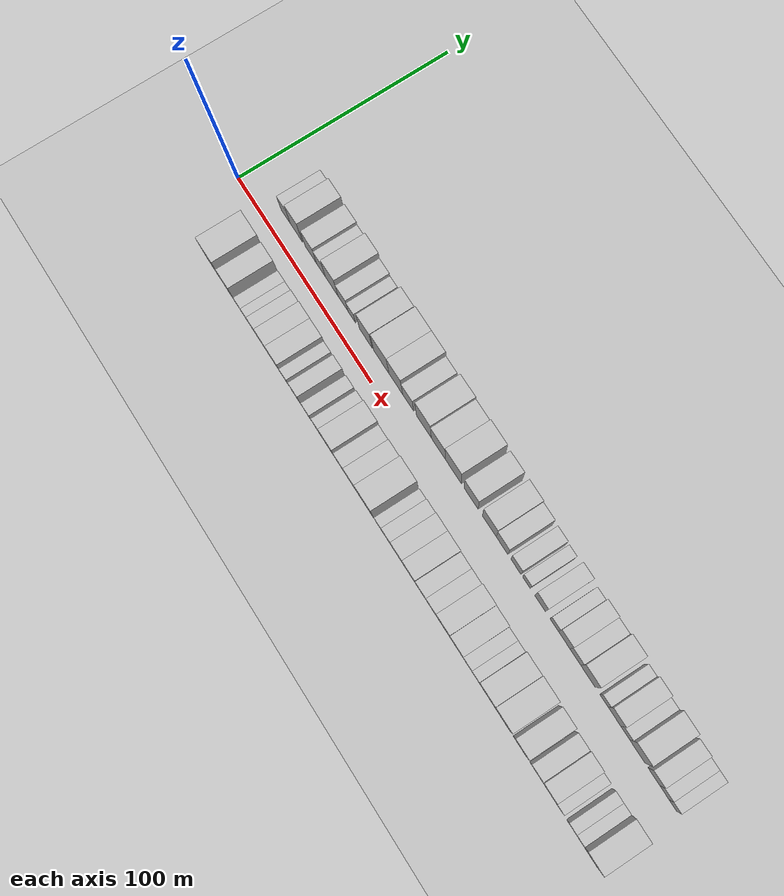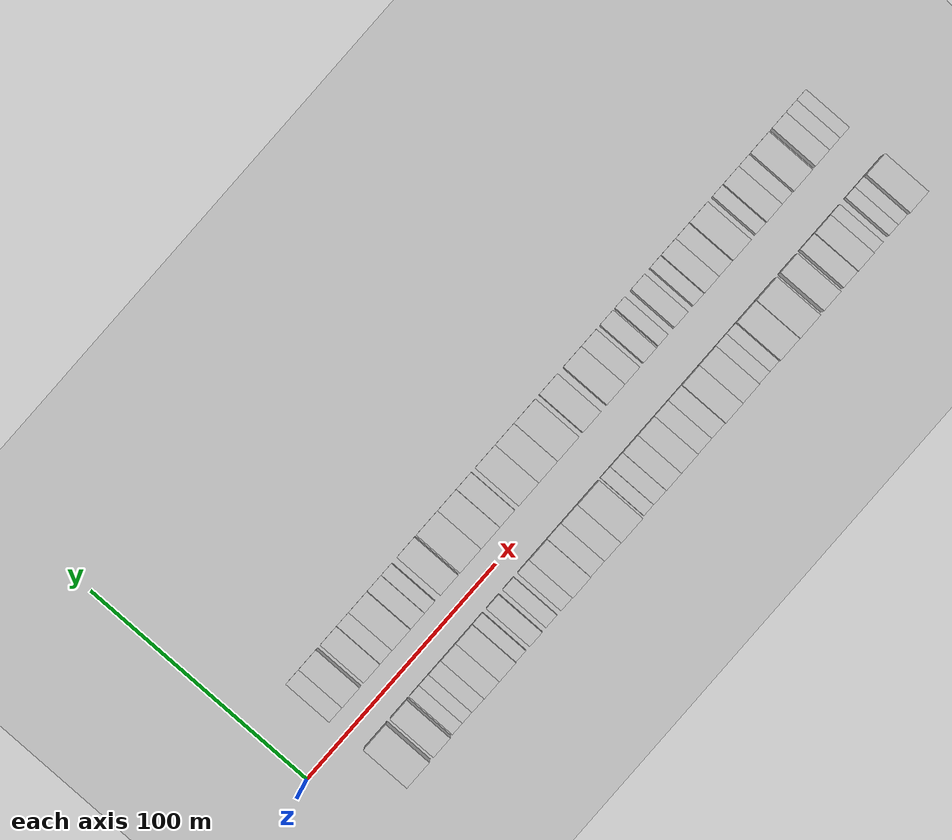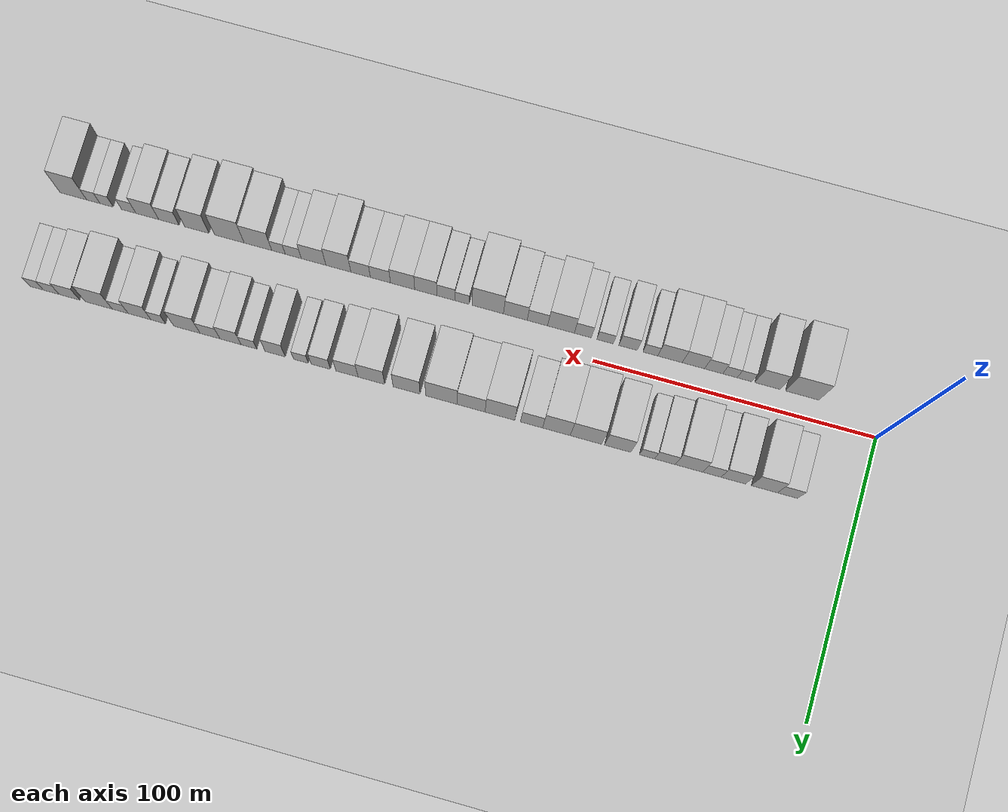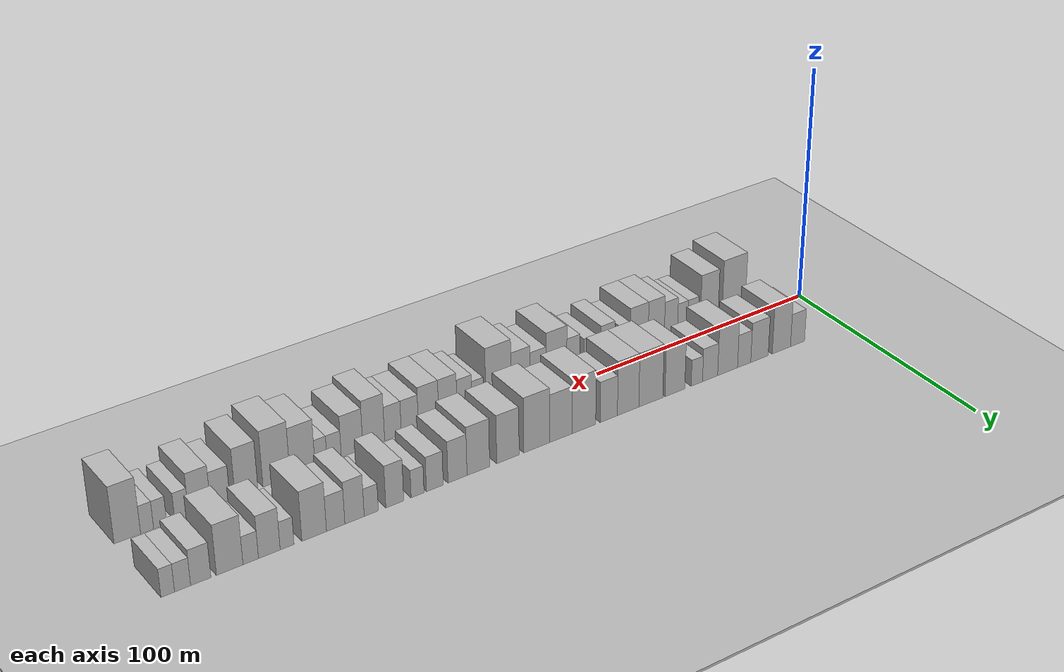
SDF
<?xml version="1.0" encoding="utf-8"?>

<sdf version="1.6">

   <world name="default">

      <gui fullscreen="0">

         <camera name="user_camera">

            <pose>-15 0 4.57585 0 0 0</pose>

            <view_controller>orbit</view_controller>

         </camera>

      </gui>

      <scene>

         <sky>

           <clouds>

             <speed>12</speed>

           </clouds>

         </sky>

         <ambient>0.4 0.4 0.4 1</ambient>

         <background>0.7 0.7 0.7 1</background>

         <shadows>1</shadows>

      </scene>

      <gravity>0 0 -9.8066</gravity>

      <magnetic_field>6e-06 2.3e-05 -4.2e-05</magnetic_field>

      <physics default="0" name="default_physics" type="ode">

         <ode>

            <solver>

               <type>quick</type>

               <iters>10</iters>

               <sor>1.0</sor>

               <use_dynamic_moi_rescaling>0</use_dynamic_moi_rescaling>

            </solver>

            <constraints>

               <cfm>0</cfm>

               <erp>0.2</erp>

               <contact_max_correcting_vel>100</contact_max_correcting_vel>

               <contact_surface_layer>0.001</contact_surface_layer>

            </constraints>

         </ode>

         <max_step_size>0.004</max_step_size>

         <real_time_factor>1</real_time_factor>

         <real_time_update_rate>250</real_time_update_rate>

      </physics>

      <light name="sun" type="directional">

         <cast_shadows>1</cast_shadows>

         <pose>0 0 10 0 0 0</pose>

         <diffuse>0.8 0.8 0.8 1</diffuse>

         <specular>0.2 0.2 0.2 1</specular>

         <attenuation>

            <range>1000</range>

            <constant>0.9</constant>

            <linear>0.01</linear>

            <quadratic>0.001</quadratic>

         </attenuation>

         <direction>-0.5 0.1 -0.9</direction>

      </light>

      <include>

         <name>ground_plane_1</name>

         <uri>model://HANNAS_ground_plane</uri>

         <pose>0 0 0  0 0 0</pose>

      </include>

      <include>

         <name>ground_plane_2</name>

         <uri>model://HANNAS_ground_plane</uri>

         <pose>100 0 0  0 0 0</pose>

      </include>

      <model name="building_1">

         <static>1</static>

         <pose frame="">24.5312 17.5000 0 0.000000 0.000000 1.570796</pose>

         <link name="link">

            <pose frame="">0 0 7.50 0 0 0</pose>

            <collision name="collision">

               <geometry>

                  <box>

                     <size>20.0000 7.0624 15.0000</size>

                  </box>

               </geometry>

               <max_contacts>10</max_contacts>

               <surface>

                  <contact>

                     <ode/>

                  </contact>

                  <bounce/>

                  <friction>

                     <torsional>

                        <ode/>

                     </torsional>

                     <ode/>

                  </friction>

               </surface>

            </collision>

            <visual name="visual">

               <cast_shadows>0</cast_shadows>

               <geometry>

                  <box>

                     <size>20.0000 7.0624 15.0000</size>

                  </box>

               </geometry>

               <material>

                  <script>

                     <uri>model://HANNAS_wall/materials/scripts</uri>

                     <uri>model://HANNAS_wall/materials/textures</uri>

                     <name>vrc/HANNAS_wall</name>

                  </script>

               </material>

            </visual>

            <self_collide>0</self_collide>

            <enable_wind>0</enable_wind>

            <kinematic>0</kinematic>

         </link>

      </model>

      <model name="building_2">

         <static>1</static>

         <pose frame="">32.6191 17.5000 0 0.000000 0.000000 1.570796</pose>

         <link name="link">

            <pose frame="">0 0 10.50 0 0 0</pose>

            <collision name="collision">

               <geometry>

                  <box>

                     <size>20.0000 9.1133 21.0000</size>

                  </box>

               </geometry>

               <max_contacts>10</max_contacts>

               <surface>

                  <contact>

                     <ode/>

                  </contact>

                  <bounce/>

                  <friction>

                     <torsional>

                        <ode/>

                     </torsional>

                     <ode/>

                  </friction>

               </surface>

            </collision>

            <visual name="visual">

               <cast_shadows>0</cast_shadows>

               <geometry>

                  <box>

                     <size>20.0000 9.1133 21.0000</size>

                  </box>

               </geometry>

               <material>

                  <script>

                     <uri>model://HANNAS_wall/materials/scripts</uri>

                     <uri>model://HANNAS_wall/materials/textures</uri>

                     <name>vrc/HANNAS_wall</name>

                  </script>

               </material>

            </visual>

            <self_collide>0</self_collide>

            <enable_wind>0</enable_wind>

            <kinematic>0</kinematic>

         </link>

      </model>

      <model name="building_3">

         <static>1</static>

         <pose frame="">43.4742 17.5000 0 0.000000 0.000000 1.570796</pose>

         <link name="link">

            <pose frame="">0 0 9.00 0 0 0</pose>

            <collision name="collision">

               <geometry>

                  <box>

                     <size>20.0000 8.5970 18.0000</size>

                  </box>

               </geometry>

               <max_contacts>10</max_contacts>

               <surface>

                  <contact>

                     <ode/>

                  </contact>

                  <bounce/>

                  <friction>

                     <torsional>

                        <ode/>

                     </torsional>

                     <ode/>

                  </friction>

               </surface>

            </collision>

            <visual name="visual">

               <cast_shadows>0</cast_shadows>

               <geometry>

                  <box>

                     <size>20.0000 8.5970 18.0000</size>

                  </box>

               </geometry>

               <material>

                  <script>

                     <uri>model://HANNAS_wall/materials/scripts</uri>

                     <uri>model://HANNAS_wall/materials/textures</uri>

                     <name>vrc/HANNAS_wall</name>

                  </script>

               </material>

            </visual>

            <self_collide>0</self_collide>

            <enable_wind>0</enable_wind>

            <kinematic>0</kinematic>

         </link>

      </model>

      <model name="building_4">

         <static>1</static>

         <pose frame="">51.0130 17.5000 0 0.000000 0.000000 1.570796</pose>

         <link name="link">

            <pose frame="">0 0 7.50 0 0 0</pose>

            <collision name="collision">

               <geometry>

                  <box>

                     <size>20.0000 6.4806 15.0000</size>

                  </box>

               </geometry>

               <max_contacts>10</max_contacts>

               <surface>

                  <contact>

                     <ode/>

                  </contact>

                  <bounce/>

                  <friction>

                     <torsional>

                        <ode/>

                     </torsional>

                     <ode/>

                  </friction>

               </surface>

            </collision>

            <visual name="visual">

               <cast_shadows>0</cast_shadows>

               <geometry>

                  <box>

                     <size>20.0000 6.4806 15.0000</size>

                  </box>

               </geometry>

               <material>

                  <script>

                     <uri>model://HANNAS_wall/materials/scripts</uri>

                     <uri>model://HANNAS_wall/materials/textures</uri>

                     <name>vrc/HANNAS_wall</name>

                  </script>

               </material>

            </visual>

            <self_collide>0</self_collide>

            <enable_wind>0</enable_wind>

            <kinematic>0</kinematic>

         </link>

      </model>

      <model name="building_5">

         <static>1</static>

         <pose frame="">59.0527 17.5000 0 0.000000 0.000000 1.570796</pose>

         <link name="link">

            <pose frame="">0 0 10.50 0 0 0</pose>

            <collision name="collision">

               <geometry>

                  <box>

                     <size>20.0000 9.5987 21.0000</size>

                  </box>

               </geometry>

               <max_contacts>10</max_contacts>

               <surface>

                  <contact>

                     <ode/>

                  </contact>

                  <bounce/>

                  <friction>

                     <torsional>

                        <ode/>

                     </torsional>

                     <ode/>

                  </friction>

               </surface>

            </collision>

            <visual name="visual">

               <cast_shadows>0</cast_shadows>

               <geometry>

                  <box>

                     <size>20.0000 9.5987 21.0000</size>

                  </box>

               </geometry>

               <material>

                  <script>

                     <uri>model://HANNAS_wall/materials/scripts</uri>

                     <uri>model://HANNAS_wall/materials/textures</uri>

                     <name>vrc/HANNAS_wall</name>

                  </script>

               </material>

            </visual>

            <self_collide>0</self_collide>

            <enable_wind>0</enable_wind>

            <kinematic>0</kinematic>

         </link>

      </model>

      <model name="building_6">

         <static>1</static>

         <pose frame="">67.4788 17.5000 0 0.000000 0.000000 1.570796</pose>

         <link name="link">

            <pose frame="">0 0 7.50 0 0 0</pose>

            <collision name="collision">

               <geometry>

                  <box>

                     <size>20.0000 7.2534 15.0000</size>

                  </box>

               </geometry>

               <max_contacts>10</max_contacts>

               <surface>

                  <contact>

                     <ode/>

                  </contact>

                  <bounce/>

                  <friction>

                     <torsional>

                        <ode/>

                     </torsional>

                     <ode/>

                  </friction>

               </surface>

            </collision>

            <visual name="visual">

               <cast_shadows>0</cast_shadows>

               <geometry>

                  <box>

                     <size>20.0000 7.2534 15.0000</size>

                  </box>

               </geometry>

               <material>

                  <script>

                     <uri>model://HANNAS_wall/materials/scripts</uri>

                     <uri>model://HANNAS_wall/materials/textures</uri>

                     <name>vrc/HANNAS_wall</name>

                  </script>

               </material>

            </visual>

            <self_collide>0</self_collide>

            <enable_wind>0</enable_wind>

            <kinematic>0</kinematic>

         </link>

      </model>

      <model name="building_7">

         <static>1</static>

         <pose frame="">73.7996 17.5000 0 0.000000 0.000000 1.570796</pose>

         <link name="link">

            <pose frame="">0 0 6.00 0 0 0</pose>

            <collision name="collision">

               <geometry>

                  <box>

                     <size>20.0000 5.3883 12.0000</size>

                  </box>

               </geometry>

               <max_contacts>10</max_contacts>

               <surface>

                  <contact>

                     <ode/>

                  </contact>

                  <bounce/>

                  <friction>

                     <torsional>

                        <ode/>

                     </torsional>

                     <ode/>

                  </friction>

               </surface>

            </collision>

            <visual name="visual">

               <cast_shadows>0</cast_shadows>

               <geometry>

                  <box>

                     <size>20.0000 5.3883 12.0000</size>

                  </box>

               </geometry>

               <material>

                  <script>

                     <uri>model://HANNAS_wall/materials/scripts</uri>

                     <uri>model://HANNAS_wall/materials/textures</uri>

                     <name>vrc/HANNAS_wall</name>

                  </script>

               </material>

            </visual>

            <self_collide>0</self_collide>

            <enable_wind>0</enable_wind>

            <kinematic>0</kinematic>

         </link>

      </model>

      <model name="building_8">

         <static>1</static>

         <pose frame="">84.1471 17.5000 0 0.000000 0.000000 1.570796</pose>

         <link name="link">

            <pose frame="">0 0 10.50 0 0 0</pose>

            <collision name="collision">

               <geometry>

                  <box>

                     <size>20.0000 9.3068 21.0000</size>

                  </box>

               </geometry>

               <max_contacts>10</max_contacts>

               <surface>

                  <contact>

                     <ode/>

                  </contact>

                  <bounce/>

                  <friction>

                     <torsional>

                        <ode/>

                     </torsional>

                     <ode/>

                  </friction>

               </surface>

            </collision>

            <visual name="visual">

               <cast_shadows>0</cast_shadows>

               <geometry>

                  <box>

                     <size>20.0000 9.3068 21.0000</size>

                  </box>

               </geometry>

               <material>

                  <script>

                     <uri>model://HANNAS_wall/materials/scripts</uri>

                     <uri>model://HANNAS_wall/materials/textures</uri>

                     <name>vrc/HANNAS_wall</name>

                  </script>

               </material>

            </visual>

            <self_collide>0</self_collide>

            <enable_wind>0</enable_wind>

            <kinematic>0</kinematic>

         </link>

      </model>

      <model name="building_9">

         <static>1</static>

         <pose frame="">95.3636 17.5000 0 0.000000 0.000000 1.570796</pose>

         <link name="link">

            <pose frame="">0 0 12.00 0 0 0</pose>

            <collision name="collision">

               <geometry>

                  <box>

                     <size>20.0000 11.1262 24.0000</size>

                  </box>

               </geometry>

               <max_contacts>10</max_contacts>

               <surface>

                  <contact>

                     <ode/>

                  </contact>

                  <bounce/>

                  <friction>

                     <torsional>

                        <ode/>

                     </torsional>

                     <ode/>

                  </friction>

               </surface>

            </collision>

            <visual name="visual">

               <cast_shadows>0</cast_shadows>

               <geometry>

                  <box>

                     <size>20.0000 11.1262 24.0000</size>

                  </box>

               </geometry>

               <material>

                  <script>

                     <uri>model://HANNAS_wall/materials/scripts</uri>

                     <uri>model://HANNAS_wall/materials/textures</uri>

                     <name>vrc/HANNAS_wall</name>

                  </script>

               </material>

            </visual>

            <self_collide>0</self_collide>

            <enable_wind>0</enable_wind>

            <kinematic>0</kinematic>

         </link>

      </model>

      <model name="building_10">

         <static>1</static>

         <pose frame="">105.8117 17.5000 0 0.000000 0.000000 1.570796</pose>

         <link name="link">

            <pose frame="">0 0 12.00 0 0 0</pose>

            <collision name="collision">

               <geometry>

                  <box>

                     <size>20.0000 9.7699 24.0000</size>

                  </box>

               </geometry>

               <max_contacts>10</max_contacts>

               <surface>

                  <contact>

                     <ode/>

                  </contact>

                  <bounce/>

                  <friction>

                     <torsional>

                        <ode/>

                     </torsional>

                     <ode/>

                  </friction>

               </surface>

            </collision>

            <visual name="visual">

               <cast_shadows>0</cast_shadows>

               <geometry>

                  <box>

                     <size>20.0000 9.7699 24.0000</size>

                  </box>

               </geometry>

               <material>

                  <script>

                     <uri>model://HANNAS_wall/materials/scripts</uri>

                     <uri>model://HANNAS_wall/materials/textures</uri>

                     <name>vrc/HANNAS_wall</name>

                  </script>

               </material>

            </visual>

            <self_collide>0</self_collide>

            <enable_wind>0</enable_wind>

            <kinematic>0</kinematic>

         </link>

      </model>

      <model name="building_11">

         <static>1</static>

         <pose frame="">114.6032 17.5000 0 0.000000 0.000000 1.570796</pose>

         <link name="link">

            <pose frame="">0 0 9.00 0 0 0</pose>

            <collision name="collision">

               <geometry>

                  <box>

                     <size>20.0000 7.8132 18.0000</size>

                  </box>

               </geometry>

               <max_contacts>10</max_contacts>

               <surface>

                  <contact>

                     <ode/>

                  </contact>

                  <bounce/>

                  <friction>

                     <torsional>

                        <ode/>

                     </torsional>

                     <ode/>

                  </friction>

               </surface>

            </collision>

            <visual name="visual">

               <cast_shadows>0</cast_shadows>

               <geometry>

                  <box>

                     <size>20.0000 7.8132 18.0000</size>

                  </box>

               </geometry>

               <material>

                  <script>

                     <uri>model://HANNAS_wall/materials/scripts</uri>

                     <uri>model://HANNAS_wall/materials/textures</uri>

                     <name>vrc/HANNAS_wall</name>

                  </script>

               </material>

            </visual>

            <self_collide>0</self_collide>

            <enable_wind>0</enable_wind>

            <kinematic>0</kinematic>

         </link>

      </model>

      <model name="building_12">

         <static>1</static>

         <pose frame="">125.7846 17.5000 0 0.000000 0.000000 1.570796</pose>

         <link name="link">

            <pose frame="">0 0 12.00 0 0 0</pose>

            <collision name="collision">

               <geometry>

                  <box>

                     <size>20.0000 10.5496 24.0000</size>

                  </box>

               </geometry>

               <max_contacts>10</max_contacts>

               <surface>

                  <contact>

                     <ode/>

                  </contact>

                  <bounce/>

                  <friction>

                     <torsional>

                        <ode/>

                     </torsional>

                     <ode/>

                  </friction>

               </surface>

            </collision>

            <visual name="visual">

               <cast_shadows>0</cast_shadows>

               <geometry>

                  <box>

                     <size>20.0000 10.5496 24.0000</size>

                  </box>

               </geometry>

               <material>

                  <script>

                     <uri>model://HANNAS_wall/materials/scripts</uri>

                     <uri>model://HANNAS_wall/materials/textures</uri>

                     <name>vrc/HANNAS_wall</name>

                  </script>

               </material>

            </visual>

            <self_collide>0</self_collide>

            <enable_wind>0</enable_wind>

            <kinematic>0</kinematic>

         </link>

      </model>

      <model name="building_13">

         <static>1</static>

         <pose frame="">136.0010 17.5000 0 0.000000 0.000000 1.570796</pose>

         <link name="link">

            <pose frame="">0 0 10.50 0 0 0</pose>

            <collision name="collision">

               <geometry>

                  <box>

                     <size>20.0000 9.8832 21.0000</size>

                  </box>

               </geometry>

               <max_contacts>10</max_contacts>

               <surface>

                  <contact>

                     <ode/>

                  </contact>

                  <bounce/>

                  <friction>

                     <torsional>

                        <ode/>

                     </torsional>

                     <ode/>

                  </friction>

               </surface>

            </collision>

            <visual name="visual">

               <cast_shadows>0</cast_shadows>

               <geometry>

                  <box>

                     <size>20.0000 9.8832 21.0000</size>

                  </box>

               </geometry>

               <material>

                  <script>

                     <uri>model://HANNAS_wall/materials/scripts</uri>

                     <uri>model://HANNAS_wall/materials/textures</uri>

                     <name>vrc/HANNAS_wall</name>

                  </script>

               </material>

            </visual>

            <self_collide>0</self_collide>

            <enable_wind>0</enable_wind>

            <kinematic>0</kinematic>

         </link>

      </model>

      <model name="building_14">

         <static>1</static>

         <pose frame="">146.5517 17.5000 0 0.000000 0.000000 1.570796</pose>

         <link name="link">

            <pose frame="">0 0 12.00 0 0 0</pose>

            <collision name="collision">

               <geometry>

                  <box>

                     <size>20.0000 11.2180 24.0000</size>

                  </box>

               </geometry>

               <max_contacts>10</max_contacts>

               <surface>

                  <contact>

                     <ode/>

                  </contact>

                  <bounce/>

                  <friction>

                     <torsional>

                        <ode/>

                     </torsional>

                     <ode/>

                  </friction>

               </surface>

            </collision>

            <visual name="visual">

               <cast_shadows>0</cast_shadows>

               <geometry>

                  <box>

                     <size>20.0000 11.2180 24.0000</size>

                  </box>

               </geometry>

               <material>

                  <script>

                     <uri>model://HANNAS_wall/materials/scripts</uri>

                     <uri>model://HANNAS_wall/materials/textures</uri>

                     <name>vrc/HANNAS_wall</name>

                  </script>

               </material>

            </visual>

            <self_collide>0</self_collide>

            <enable_wind>0</enable_wind>

            <kinematic>0</kinematic>

         </link>

      </model>

      <model name="building_15">

         <static>1</static>

         <pose frame="">158.9572 17.5000 0 0.000000 0.000000 1.570796</pose>

         <link name="link">

            <pose frame="">0 0 10.50 0 0 0</pose>

            <collision name="collision">

               <geometry>

                  <box>

                     <size>20.0000 9.5930 21.0000</size>

                  </box>

               </geometry>

               <max_contacts>10</max_contacts>

               <surface>

                  <contact>

                     <ode/>

                  </contact>

                  <bounce/>

                  <friction>

                     <torsional>

                        <ode/>

                     </torsional>

                     <ode/>

                  </friction>

               </surface>

            </collision>

            <visual name="visual">

               <cast_shadows>0</cast_shadows>

               <geometry>

                  <box>

                     <size>20.0000 9.5930 21.0000</size>

                  </box>

               </geometry>

               <material>

                  <script>

                     <uri>model://HANNAS_wall/materials/scripts</uri>

                     <uri>model://HANNAS_wall/materials/textures</uri>

                     <name>vrc/HANNAS_wall</name>

                  </script>

               </material>

            </visual>

            <self_collide>0</self_collide>

            <enable_wind>0</enable_wind>

            <kinematic>0</kinematic>

         </link>

      </model>

      <model name="building_16">

         <static>1</static>

         <pose frame="">171.5148 17.5000 0 0.000000 0.000000 1.570796</pose>

         <link name="link">

            <pose frame="">0 0 10.50 0 0 0</pose>

            <collision name="collision">

               <geometry>

                  <box>

                     <size>20.0000 9.5221 21.0000</size>

                  </box>

               </geometry>

               <max_contacts>10</max_contacts>

               <surface>

                  <contact>

                     <ode/>

                  </contact>

                  <bounce/>

                  <friction>

                     <torsional>

                        <ode/>

                     </torsional>

                     <ode/>

                  </friction>

               </surface>

            </collision>

            <visual name="visual">

               <cast_shadows>0</cast_shadows>

               <geometry>

                  <box>

                     <size>20.0000 9.5221 21.0000</size>

                  </box>

               </geometry>

               <material>

                  <script>

                     <uri>model://HANNAS_wall/materials/scripts</uri>

                     <uri>model://HANNAS_wall/materials/textures</uri>

                     <name>vrc/HANNAS_wall</name>

                  </script>

               </material>

            </visual>

            <self_collide>0</self_collide>

            <enable_wind>0</enable_wind>

            <kinematic>0</kinematic>

         </link>

      </model>

      <model name="building_17">

         <static>1</static>

         <pose frame="">180.2313 17.5000 0 0.000000 0.000000 1.570796</pose>

         <link name="link">

            <pose frame="">0 0 9.00 0 0 0</pose>

            <collision name="collision">

               <geometry>

                  <box>

                     <size>20.0000 7.9109 18.0000</size>

                  </box>

               </geometry>

               <max_contacts>10</max_contacts>

               <surface>

                  <contact>

                     <ode/>

                  </contact>

                  <bounce/>

                  <friction>

                     <torsional>

                        <ode/>

                     </torsional>

                     <ode/>

                  </friction>

               </surface>

            </collision>

            <visual name="visual">

               <cast_shadows>0</cast_shadows>

               <geometry>

                  <box>

                     <size>20.0000 7.9109 18.0000</size>

                  </box>

               </geometry>

               <material>

                  <script>

                     <uri>model://HANNAS_wall/materials/scripts</uri>

                     <uri>model://HANNAS_wall/materials/textures</uri>

                     <name>vrc/HANNAS_wall</name>

                  </script>

               </material>

            </visual>

            <self_collide>0</self_collide>

            <enable_wind>0</enable_wind>

            <kinematic>0</kinematic>

         </link>

      </model>

      <model name="building_18">

         <static>1</static>

         <pose frame="">189.6379 17.5000 0 0.000000 0.000000 1.570796</pose>

         <link name="link">

            <pose frame="">0 0 7.50 0 0 0</pose>

            <collision name="collision">

               <geometry>

                  <box>

                     <size>20.0000 6.9022 15.0000</size>

                  </box>

               </geometry>

               <max_contacts>10</max_contacts>

               <surface>

                  <contact>

                     <ode/>

                  </contact>

                  <bounce/>

                  <friction>

                     <torsional>

                        <ode/>

                     </torsional>

                     <ode/>

                  </friction>

               </surface>

            </collision>

            <visual name="visual">

               <cast_shadows>0</cast_shadows>

               <geometry>

                  <box>

                     <size>20.0000 6.9022 15.0000</size>

                  </box>

               </geometry>

               <material>

                  <script>

                     <uri>model://HANNAS_wall/materials/scripts</uri>

                     <uri>model://HANNAS_wall/materials/textures</uri>

                     <name>vrc/HANNAS_wall</name>

                  </script>

               </material>

            </visual>

            <self_collide>0</self_collide>

            <enable_wind>0</enable_wind>

            <kinematic>0</kinematic>

         </link>

      </model>

      <model name="building_19">

         <static>1</static>

         <pose frame="">196.7116 17.5000 0 0.000000 0.000000 1.570796</pose>

         <link name="link">

            <pose frame="">0 0 6.00 0 0 0</pose>

            <collision name="collision">

               <geometry>

                  <box>

                     <size>20.0000 5.2452 12.0000</size>

                  </box>

               </geometry>

               <max_contacts>10</max_contacts>

               <surface>

                  <contact>

                     <ode/>

                  </contact>

                  <bounce/>

                  <friction>

                     <torsional>

                        <ode/>

                     </torsional>

                     <ode/>

                  </friction>

               </surface>

            </collision>

            <visual name="visual">

               <cast_shadows>0</cast_shadows>

               <geometry>

                  <box>

                     <size>20.0000 5.2452 12.0000</size>

                  </box>

               </geometry>

               <material>

                  <script>

                     <uri>model://HANNAS_wall/materials/scripts</uri>

                     <uri>model://HANNAS_wall/materials/textures</uri>

                     <name>vrc/HANNAS_wall</name>

                  </script>

               </material>

            </visual>

            <self_collide>0</self_collide>

            <enable_wind>0</enable_wind>

            <kinematic>0</kinematic>

         </link>

      </model>

      <model name="building_20">

         <static>1</static>

         <pose frame="">205.9429 17.5000 0 0.000000 0.000000 1.570796</pose>

         <link name="link">

            <pose frame="">0 0 9.00 0 0 0</pose>

            <collision name="collision">

               <geometry>

                  <box>

                     <size>20.0000 7.2174 18.0000</size>

                  </box>

               </geometry>

               <max_contacts>10</max_contacts>

               <surface>

                  <contact>

                     <ode/>

                  </contact>

                  <bounce/>

                  <friction>

                     <torsional>

                        <ode/>

                     </torsional>

                     <ode/>

                  </friction>

               </surface>

            </collision>

            <visual name="visual">

               <cast_shadows>0</cast_shadows>

               <geometry>

                  <box>

                     <size>20.0000 7.2174 18.0000</size>

                  </box>

               </geometry>

               <material>

                  <script>

                     <uri>model://HANNAS_wall/materials/scripts</uri>

                     <uri>model://HANNAS_wall/materials/textures</uri>

                     <name>vrc/HANNAS_wall</name>

                  </script>

               </material>

            </visual>

            <self_collide>0</self_collide>

            <enable_wind>0</enable_wind>

            <kinematic>0</kinematic>

         </link>

      </model>

      <model name="building_21">

         <static>1</static>

         <pose frame="">215.3597 17.5000 0 0.000000 0.000000 1.570796</pose>

         <link name="link">

            <pose frame="">0 0 6.00 0 0 0</pose>

            <collision name="collision">

               <geometry>

                  <box>

                     <size>20.0000 5.6162 12.0000</size>

                  </box>

               </geometry>

               <max_contacts>10</max_contacts>

               <surface>

                  <contact>

                     <ode/>

                  </contact>

                  <bounce/>

                  <friction>

                     <torsional>

                        <ode/>

                     </torsional>

                     <ode/>

                  </friction>

               </surface>

            </collision>

            <visual name="visual">

               <cast_shadows>0</cast_shadows>

               <geometry>

                  <box>

                     <size>20.0000 5.6162 12.0000</size>

                  </box>

               </geometry>

               <material>

                  <script>

                     <uri>model://HANNAS_wall/materials/scripts</uri>

                     <uri>model://HANNAS_wall/materials/textures</uri>

                     <name>vrc/HANNAS_wall</name>

                  </script>

               </material>

            </visual>

            <self_collide>0</self_collide>

            <enable_wind>0</enable_wind>

            <kinematic>0</kinematic>

         </link>

      </model>

      <model name="building_22">

         <static>1</static>

         <pose frame="">221.9842 17.5000 0 0.000000 0.000000 1.570796</pose>

         <link name="link">

            <pose frame="">0 0 9.00 0 0 0</pose>

            <collision name="collision">

               <geometry>

                  <box>

                     <size>20.0000 7.6328 18.0000</size>

                  </box>

               </geometry>

               <max_contacts>10</max_contacts>

               <surface>

                  <contact>

                     <ode/>

                  </contact>

                  <bounce/>

                  <friction>

                     <torsional>

                        <ode/>

                     </torsional>

                     <ode/>

                  </friction>

               </surface>

            </collision>

            <visual name="visual">

               <cast_shadows>0</cast_shadows>

               <geometry>

                  <box>

                     <size>20.0000 7.6328 18.0000</size>

                  </box>

               </geometry>

               <material>

                  <script>

                     <uri>model://HANNAS_wall/materials/scripts</uri>

                     <uri>model://HANNAS_wall/materials/textures</uri>

                     <name>vrc/HANNAS_wall</name>

                  </script>

               </material>

            </visual>

            <self_collide>0</self_collide>

            <enable_wind>0</enable_wind>

            <kinematic>0</kinematic>

         </link>

      </model>

      <model name="building_23">

         <static>1</static>

         <pose frame="">229.3829 17.5000 0 0.000000 0.000000 1.570796</pose>

         <link name="link">

            <pose frame="">0 0 7.50 0 0 0</pose>

            <collision name="collision">

               <geometry>

                  <box>

                     <size>20.0000 7.1647 15.0000</size>

                  </box>

               </geometry>

               <max_contacts>10</max_contacts>

               <surface>

                  <contact>

                     <ode/>

                  </contact>

                  <bounce/>

                  <friction>

                     <torsional>

                        <ode/>

                     </torsional>

                     <ode/>

                  </friction>

               </surface>

            </collision>

            <visual name="visual">

               <cast_shadows>0</cast_shadows>

               <geometry>

                  <box>

                     <size>20.0000 7.1647 15.0000</size>

                  </box>

               </geometry>

               <material>

                  <script>

                     <uri>model://HANNAS_wall/materials/scripts</uri>

                     <uri>model://HANNAS_wall/materials/textures</uri>

                     <name>vrc/HANNAS_wall</name>

                  </script>

               </material>

            </visual>

            <self_collide>0</self_collide>

            <enable_wind>0</enable_wind>

            <kinematic>0</kinematic>

         </link>

      </model>

      <model name="building_24">

         <static>1</static>

         <pose frame="">237.7203 17.5000 0 0.000000 0.000000 1.570796</pose>

         <link name="link">

            <pose frame="">0 0 10.50 0 0 0</pose>

            <collision name="collision">

               <geometry>

                  <box>

                     <size>20.0000 9.5099 21.0000</size>

                  </box>

               </geometry>

               <max_contacts>10</max_contacts>

               <surface>

                  <contact>

                     <ode/>

                  </contact>

                  <bounce/>

                  <friction>

                     <torsional>

                        <ode/>

                     </torsional>

                     <ode/>

                  </friction>

               </surface>

            </collision>

            <visual name="visual">

               <cast_shadows>0</cast_shadows>

               <geometry>

                  <box>

                     <size>20.0000 9.5099 21.0000</size>

                  </box>

               </geometry>

               <material>

                  <script>

                     <uri>model://HANNAS_wall/materials/scripts</uri>

                     <uri>model://HANNAS_wall/materials/textures</uri>

                     <name>vrc/HANNAS_wall</name>

                  </script>

               </material>

            </visual>

            <self_collide>0</self_collide>

            <enable_wind>0</enable_wind>

            <kinematic>0</kinematic>

         </link>

      </model>

      <model name="building_25">

         <static>1</static>

         <pose frame="">248.1216 17.5000 0 0.000000 0.000000 1.570796</pose>

         <link name="link">

            <pose frame="">0 0 6.00 0 0 0</pose>

            <collision name="collision">

               <geometry>

                  <box>

                     <size>20.0000 5.2927 12.0000</size>

                  </box>

               </geometry>

               <max_contacts>10</max_contacts>

               <surface>

                  <contact>

                     <ode/>

                  </contact>

                  <bounce/>

                  <friction>

                     <torsional>

                        <ode/>

                     </torsional>

                     <ode/>

                  </friction>

               </surface>

            </collision>

            <visual name="visual">

               <cast_shadows>0</cast_shadows>

               <geometry>

                  <box>

                     <size>20.0000 5.2927 12.0000</size>

                  </box>

               </geometry>

               <material>

                  <script>

                     <uri>model://HANNAS_wall/materials/scripts</uri>

                     <uri>model://HANNAS_wall/materials/textures</uri>

                     <name>vrc/HANNAS_wall</name>

                  </script>

               </material>

            </visual>

            <self_collide>0</self_collide>

            <enable_wind>0</enable_wind>

            <kinematic>0</kinematic>

         </link>

      </model>

      <model name="building_26">

         <static>1</static>

         <pose frame="">254.8613 17.5000 0 0.000000 0.000000 1.570796</pose>

         <link name="link">

            <pose frame="">0 0 9.00 0 0 0</pose>

            <collision name="collision">

               <geometry>

                  <box>

                     <size>20.0000 8.1869 18.0000</size>

                  </box>

               </geometry>

               <max_contacts>10</max_contacts>

               <surface>

                  <contact>

                     <ode/>

                  </contact>

                  <bounce/>

                  <friction>

                     <torsional>

                        <ode/>

                     </torsional>

                     <ode/>

                  </friction>

               </surface>

            </collision>

            <visual name="visual">

               <cast_shadows>0</cast_shadows>

               <geometry>

                  <box>

                     <size>20.0000 8.1869 18.0000</size>

                  </box>

               </geometry>

               <material>

                  <script>

                     <uri>model://HANNAS_wall/materials/scripts</uri>

                     <uri>model://HANNAS_wall/materials/textures</uri>

                     <name>vrc/HANNAS_wall</name>

                  </script>

               </material>

            </visual>

            <self_collide>0</self_collide>

            <enable_wind>0</enable_wind>

            <kinematic>0</kinematic>

         </link>

      </model>

      <model name="building_27">

         <static>1</static>

         <pose frame="">261.8539 17.5000 0 0.000000 0.000000 1.570796</pose>

         <link name="link">

            <pose frame="">0 0 6.00 0 0 0</pose>

            <collision name="collision">

               <geometry>

                  <box>

                     <size>20.0000 5.7983 12.0000</size>

                  </box>

               </geometry>

               <max_contacts>10</max_contacts>

               <surface>

                  <contact>

                     <ode/>

                  </contact>

                  <bounce/>

                  <friction>

                     <torsional>

                        <ode/>

                     </torsional>

                     <ode/>

                  </friction>

               </surface>

            </collision>

            <visual name="visual">

               <cast_shadows>0</cast_shadows>

               <geometry>

                  <box>

                     <size>20.0000 5.7983 12.0000</size>

                  </box>

               </geometry>

               <material>

                  <script>

                     <uri>model://HANNAS_wall/materials/scripts</uri>

                     <uri>model://HANNAS_wall/materials/textures</uri>

                     <name>vrc/HANNAS_wall</name>

                  </script>

               </material>

            </visual>

            <self_collide>0</self_collide>

            <enable_wind>0</enable_wind>

            <kinematic>0</kinematic>

         </link>

      </model>

      <model name="building_28">

         <static>1</static>

         <pose frame="">269.6706 17.5000 0 0.000000 0.000000 1.570796</pose>

         <link name="link">

            <pose frame="">0 0 10.50 0 0 0</pose>

            <collision name="collision">

               <geometry>

                  <box>

                     <size>20.0000 9.8350 21.0000</size>

                  </box>

               </geometry>

               <max_contacts>10</max_contacts>

               <surface>

                  <contact>

                     <ode/>

                  </contact>

                  <bounce/>

                  <friction>

                     <torsional>

                        <ode/>

                     </torsional>

                     <ode/>

                  </friction>

               </surface>

            </collision>

            <visual name="visual">

               <cast_shadows>0</cast_shadows>

               <geometry>

                  <box>

                     <size>20.0000 9.8350 21.0000</size>

                  </box>

               </geometry>

               <material>

                  <script>

                     <uri>model://HANNAS_wall/materials/scripts</uri>

                     <uri>model://HANNAS_wall/materials/textures</uri>

                     <name>vrc/HANNAS_wall</name>

                  </script>

               </material>

            </visual>

            <self_collide>0</self_collide>

            <enable_wind>0</enable_wind>

            <kinematic>0</kinematic>

         </link>

      </model>

      <model name="building_29">

         <static>1</static>

         <pose frame="">280.2941 17.5000 0 0.000000 0.000000 1.570796</pose>

         <link name="link">

            <pose frame="">0 0 7.50 0 0 0</pose>

            <collision name="collision">

               <geometry>

                  <box>

                     <size>20.0000 7.4121 15.0000</size>

                  </box>

               </geometry>

               <max_contacts>10</max_contacts>

               <surface>

                  <contact>

                     <ode/>

                  </contact>

                  <bounce/>

                  <friction>

                     <torsional>

                        <ode/>

                     </torsional>

                     <ode/>

                  </friction>

               </surface>

            </collision>

            <visual name="visual">

               <cast_shadows>0</cast_shadows>

               <geometry>

                  <box>

                     <size>20.0000 7.4121 15.0000</size>

                  </box>

               </geometry>

               <material>

                  <script>

                     <uri>model://HANNAS_wall/materials/scripts</uri>

                     <uri>model://HANNAS_wall/materials/textures</uri>

                     <name>vrc/HANNAS_wall</name>

                  </script>

               </material>

            </visual>

            <self_collide>0</self_collide>

            <enable_wind>0</enable_wind>

            <kinematic>0</kinematic>

         </link>

      </model>

      <model name="building_30">

         <static>1</static>

         <pose frame="">286.9088 17.5000 0 0.000000 0.000000 1.570796</pose>

         <link name="link">

            <pose frame="">0 0 6.00 0 0 0</pose>

            <collision name="collision">

               <geometry>

                  <box>

                     <size>20.0000 5.8172 12.0000</size>

                  </box>

               </geometry>

               <max_contacts>10</max_contacts>

               <surface>

                  <contact>

                     <ode/>

                  </contact>

                  <bounce/>

                  <friction>

                     <torsional>

                        <ode/>

                     </torsional>

                     <ode/>

                  </friction>

               </surface>

            </collision>

            <visual name="visual">

               <cast_shadows>0</cast_shadows>

               <geometry>

                  <box>

                     <size>20.0000 5.8172 12.0000</size>

                  </box>

               </geometry>

               <material>

                  <script>

                     <uri>model://HANNAS_wall/materials/scripts</uri>

                     <uri>model://HANNAS_wall/materials/textures</uri>

                     <name>vrc/HANNAS_wall</name>

                  </script>

               </material>

            </visual>

            <self_collide>0</self_collide>

            <enable_wind>0</enable_wind>

            <kinematic>0</kinematic>

         </link>

      </model>

      <model name="building_31">

         <static>1</static>

         <pose frame="">292.2611 17.5000 0 0.000000 0.000000 1.570796</pose>

         <link name="link">

            <pose frame="">0 0 6.00 0 0 0</pose>

            <collision name="collision">

               <geometry>

                  <box>

                     <size>20.0000 4.8874 12.0000</size>

                  </box>

               </geometry>

               <max_contacts>10</max_contacts>

               <surface>

                  <contact>

                     <ode/>

                  </contact>

                  <bounce/>

                  <friction>

                     <torsional>

                        <ode/>

                     </torsional>

                     <ode/>

                  </friction>

               </surface>

            </collision>

            <visual name="visual">

               <cast_shadows>0</cast_shadows>

               <geometry>

                  <box>

                     <size>20.0000 4.8874 12.0000</size>

                  </box>

               </geometry>

               <material>

                  <script>

                     <uri>model://HANNAS_wall/materials/scripts</uri>

                     <uri>model://HANNAS_wall/materials/textures</uri>

                     <name>vrc/HANNAS_wall</name>

                  </script>

               </material>

            </visual>

            <self_collide>0</self_collide>

            <enable_wind>0</enable_wind>

            <kinematic>0</kinematic>

         </link>

      </model>

      <model name="building_32">

         <static>1</static>

         <pose frame="">27.9075 -17.5000 0 0.000000 0.000000 1.570796</pose>

         <link name="link">

            <pose frame="">0 0 12.00 0 0 0</pose>

            <collision name="collision">

               <geometry>

                  <box>

                     <size>20.0000 11.8150 24.0000</size>

                  </box>

               </geometry>

               <max_contacts>10</max_contacts>

               <surface>

                  <contact>

                     <ode/>

                  </contact>

                  <bounce/>

                  <friction>

                     <torsional>

                        <ode/>

                     </torsional>

                     <ode/>

                  </friction>

               </surface>

            </collision>

            <visual name="visual">

               <cast_shadows>0</cast_shadows>

               <geometry>

                  <box>

                     <size>20.0000 11.8150 24.0000</size>

                  </box>

               </geometry>

               <material>

                  <script>

                     <uri>model://HANNAS_wall/materials/scripts</uri>

                     <uri>model://HANNAS_wall/materials/textures</uri>

                     <name>vrc/HANNAS_wall</name>

                  </script>

               </material>

            </visual>

            <self_collide>0</self_collide>

            <enable_wind>0</enable_wind>

            <kinematic>0</kinematic>

         </link>

      </model>

      <model name="building_33">

         <static>1</static>

         <pose frame="">40.2656 -17.5000 0 0.000000 0.000000 1.570796</pose>

         <link name="link">

            <pose frame="">0 0 10.50 0 0 0</pose>

            <collision name="collision">

               <geometry>

                  <box>

                     <size>20.0000 8.9013 21.0000</size>

                  </box>

               </geometry>

               <max_contacts>10</max_contacts>

               <surface>

                  <contact>

                     <ode/>

                  </contact>

                  <bounce/>

                  <friction>

                     <torsional>

                        <ode/>

                     </torsional>

                     <ode/>

                  </friction>

               </surface>

            </collision>

            <visual name="visual">

               <cast_shadows>0</cast_shadows>

               <geometry>

                  <box>

                     <size>20.0000 8.9013 21.0000</size>

                  </box>

               </geometry>

               <material>

                  <script>

                     <uri>model://HANNAS_wall/materials/scripts</uri>

                     <uri>model://HANNAS_wall/materials/textures</uri>

                     <name>vrc/HANNAS_wall</name>

                  </script>

               </material>

            </visual>

            <self_collide>0</self_collide>

            <enable_wind>0</enable_wind>

            <kinematic>0</kinematic>

         </link>

      </model>

      <model name="building_34">

         <static>1</static>

         <pose frame="">48.3265 -17.5000 0 0.000000 0.000000 1.570796</pose>

         <link name="link">

            <pose frame="">0 0 6.00 0 0 0</pose>

            <collision name="collision">

               <geometry>

                  <box>

                     <size>20.0000 5.2206 12.0000</size>

                  </box>

               </geometry>

               <max_contacts>10</max_contacts>

               <surface>

                  <contact>

                     <ode/>

                  </contact>

                  <bounce/>

                  <friction>

                     <torsional>

                        <ode/>

                     </torsional>

                     <ode/>

                  </friction>

               </surface>

            </collision>

            <visual name="visual">

               <cast_shadows>0</cast_shadows>

               <geometry>

                  <box>

                     <size>20.0000 5.2206 12.0000</size>

                  </box>

               </geometry>

               <material>

                  <script>

                     <uri>model://HANNAS_wall/materials/scripts</uri>

                     <uri>model://HANNAS_wall/materials/textures</uri>

                     <name>vrc/HANNAS_wall</name>

                  </script>

               </material>

            </visual>

            <self_collide>0</self_collide>

            <enable_wind>0</enable_wind>

            <kinematic>0</kinematic>

         </link>

      </model>

      <model name="building_35">

         <static>1</static>

         <pose frame="">53.4964 -17.5000 0 0.000000 0.000000 1.570796</pose>

         <link name="link">

            <pose frame="">0 0 6.00 0 0 0</pose>

            <collision name="collision">

               <geometry>

                  <box>

                     <size>20.0000 5.1192 12.0000</size>

                  </box>

               </geometry>

               <max_contacts>10</max_contacts>

               <surface>

                  <contact>

                     <ode/>

                  </contact>

                  <bounce/>

                  <friction>

                     <torsional>

                        <ode/>

                     </torsional>

                     <ode/>

                  </friction>

               </surface>

            </collision>

            <visual name="visual">

               <cast_shadows>0</cast_shadows>

               <geometry>

                  <box>

                     <size>20.0000 5.1192 12.0000</size>

                  </box>

               </geometry>

               <material>

                  <script>

                     <uri>model://HANNAS_wall/materials/scripts</uri>

                     <uri>model://HANNAS_wall/materials/textures</uri>

                     <name>vrc/HANNAS_wall</name>

                  </script>

               </material>

            </visual>

            <self_collide>0</self_collide>

            <enable_wind>0</enable_wind>

            <kinematic>0</kinematic>

         </link>

      </model>

      <model name="building_36">

         <static>1</static>

         <pose frame="">59.2746 -17.5000 0 0.000000 0.000000 1.570796</pose>

         <link name="link">

            <pose frame="">0 0 7.50 0 0 0</pose>

            <collision name="collision">

               <geometry>

                  <box>

                     <size>20.0000 6.4372 15.0000</size>

                  </box>

               </geometry>

               <max_contacts>10</max_contacts>

               <surface>

                  <contact>

                     <ode/>

                  </contact>

                  <bounce/>

                  <friction>

                     <torsional>

                        <ode/>

                     </torsional>

                     <ode/>

                  </friction>

               </surface>

            </collision>

            <visual name="visual">

               <cast_shadows>0</cast_shadows>

               <geometry>

                  <box>

                     <size>20.0000 6.4372 15.0000</size>

                  </box>

               </geometry>

               <material>

                  <script>

                     <uri>model://HANNAS_wall/materials/scripts</uri>

                     <uri>model://HANNAS_wall/materials/textures</uri>

                     <name>vrc/HANNAS_wall</name>

                  </script>

               </material>

            </visual>

            <self_collide>0</self_collide>

            <enable_wind>0</enable_wind>

            <kinematic>0</kinematic>

         </link>

      </model>

      <model name="building_37">

         <static>1</static>

         <pose frame="">66.4505 -17.5000 0 0.000000 0.000000 1.570796</pose>

         <link name="link">

            <pose frame="">0 0 9.00 0 0 0</pose>

            <collision name="collision">

               <geometry>

                  <box>

                     <size>20.0000 7.9146 18.0000</size>

                  </box>

               </geometry>

               <max_contacts>10</max_contacts>

               <surface>

                  <contact>

                     <ode/>

                  </contact>

                  <bounce/>

                  <friction>

                     <torsional>

                        <ode/>

                     </torsional>

                     <ode/>

                  </friction>

               </surface>

            </collision>

            <visual name="visual">

               <cast_shadows>0</cast_shadows>

               <geometry>

                  <box>

                     <size>20.0000 7.9146 18.0000</size>

                  </box>

               </geometry>

               <material>

                  <script>

                     <uri>model://HANNAS_wall/materials/scripts</uri>

                     <uri>model://HANNAS_wall/materials/textures</uri>

                     <name>vrc/HANNAS_wall</name>

                  </script>

               </material>

            </visual>

            <self_collide>0</self_collide>

            <enable_wind>0</enable_wind>

            <kinematic>0</kinematic>

         </link>

      </model>

      <model name="building_38">

         <static>1</static>

         <pose frame="">74.7736 -17.5000 0 0.000000 0.000000 1.570796</pose>

         <link name="link">

            <pose frame="">0 0 9.00 0 0 0</pose>

            <collision name="collision">

               <geometry>

                  <box>

                     <size>20.0000 8.7315 18.0000</size>

                  </box>

               </geometry>

               <max_contacts>10</max_contacts>

               <surface>

                  <contact>

                     <ode/>

                  </contact>

                  <bounce/>

                  <friction>

                     <torsional>

                        <ode/>

                     </torsional>

                     <ode/>

                  </friction>

               </surface>

            </collision>

            <visual name="visual">

               <cast_shadows>0</cast_shadows>

               <geometry>

                  <box>

                     <size>20.0000 8.7315 18.0000</size>

                  </box>

               </geometry>

               <material>

                  <script>

                     <uri>model://HANNAS_wall/materials/scripts</uri>

                     <uri>model://HANNAS_wall/materials/textures</uri>

                     <name>vrc/HANNAS_wall</name>

                  </script>

               </material>

            </visual>

            <self_collide>0</self_collide>

            <enable_wind>0</enable_wind>

            <kinematic>0</kinematic>

         </link>

      </model>

      <model name="building_39">

         <static>1</static>

         <pose frame="">81.7462 -17.5000 0 0.000000 0.000000 1.570796</pose>

         <link name="link">

            <pose frame="">0 0 6.00 0 0 0</pose>

            <collision name="collision">

               <geometry>

                  <box>

                     <size>20.0000 5.2136 12.0000</size>

                  </box>

               </geometry>

               <max_contacts>10</max_contacts>

               <surface>

                  <contact>

                     <ode/>

                  </contact>

                  <bounce/>

                  <friction>

                     <torsional>

                        <ode/>

                     </torsional>

                     <ode/>

                  </friction>

               </surface>

            </collision>

            <visual name="visual">

               <cast_shadows>0</cast_shadows>

               <geometry>

                  <box>

                     <size>20.0000 5.2136 12.0000</size>

                  </box>

               </geometry>

               <material>

                  <script>

                     <uri>model://HANNAS_wall/materials/scripts</uri>

                     <uri>model://HANNAS_wall/materials/textures</uri>

                     <name>vrc/HANNAS_wall</name>

                  </script>

               </material>

            </visual>

            <self_collide>0</self_collide>

            <enable_wind>0</enable_wind>

            <kinematic>0</kinematic>

         </link>

      </model>

      <model name="building_40">

         <static>1</static>

         <pose frame="">89.6417 -17.5000 0 0.000000 0.000000 1.570796</pose>

         <link name="link">

            <pose frame="">0 0 7.50 0 0 0</pose>

            <collision name="collision">

               <geometry>

                  <box>

                     <size>20.0000 6.5774 15.0000</size>

                  </box>

               </geometry>

               <max_contacts>10</max_contacts>

               <surface>

                  <contact>

                     <ode/>

                  </contact>

                  <bounce/>

                  <friction>

                     <torsional>

                        <ode/>

                     </torsional>

                     <ode/>

                  </friction>

               </surface>

            </collision>

            <visual name="visual">

               <cast_shadows>0</cast_shadows>

               <geometry>

                  <box>

                     <size>20.0000 6.5774 15.0000</size>

                  </box>

               </geometry>

               <material>

                  <script>

                     <uri>model://HANNAS_wall/materials/scripts</uri>

                     <uri>model://HANNAS_wall/materials/textures</uri>

                     <name>vrc/HANNAS_wall</name>

                  </script>

               </material>

            </visual>

            <self_collide>0</self_collide>

            <enable_wind>0</enable_wind>

            <kinematic>0</kinematic>

         </link>

      </model>

      <model name="building_41">

         <static>1</static>

         <pose frame="">97.8533 -17.5000 0 0.000000 0.000000 1.570796</pose>

         <link name="link">

            <pose frame="">0 0 6.00 0 0 0</pose>

            <collision name="collision">

               <geometry>

                  <box>

                     <size>20.0000 5.8459 12.0000</size>

                  </box>

               </geometry>

               <max_contacts>10</max_contacts>

               <surface>

                  <contact>

                     <ode/>

                  </contact>

                  <bounce/>

                  <friction>

                     <torsional>

                        <ode/>

                     </torsional>

                     <ode/>

                  </friction>

               </surface>

            </collision>

            <visual name="visual">

               <cast_shadows>0</cast_shadows>

               <geometry>

                  <box>

                     <size>20.0000 5.8459 12.0000</size>

                  </box>

               </geometry>

               <material>

                  <script>

                     <uri>model://HANNAS_wall/materials/scripts</uri>

                     <uri>model://HANNAS_wall/materials/textures</uri>

                     <name>vrc/HANNAS_wall</name>

                  </script>

               </material>

            </visual>

            <self_collide>0</self_collide>

            <enable_wind>0</enable_wind>

            <kinematic>0</kinematic>

         </link>

      </model>

      <model name="building_42">

         <static>1</static>

         <pose frame="">105.8094 -17.5000 0 0.000000 0.000000 1.570796</pose>

         <link name="link">

            <pose frame="">0 0 7.50 0 0 0</pose>

            <collision name="collision">

               <geometry>

                  <box>

                     <size>20.0000 6.0663 15.0000</size>

                  </box>

               </geometry>

               <max_contacts>10</max_contacts>

               <surface>

                  <contact>

                     <ode/>

                  </contact>

                  <bounce/>

                  <friction>

                     <torsional>

                        <ode/>

                     </torsional>

                     <ode/>

                  </friction>

               </surface>

            </collision>

            <visual name="visual">

               <cast_shadows>0</cast_shadows>

               <geometry>

                  <box>

                     <size>20.0000 6.0663 15.0000</size>

                  </box>

               </geometry>

               <material>

                  <script>

                     <uri>model://HANNAS_wall/materials/scripts</uri>

                     <uri>model://HANNAS_wall/materials/textures</uri>

                     <name>vrc/HANNAS_wall</name>

                  </script>

               </material>

            </visual>

            <self_collide>0</self_collide>

            <enable_wind>0</enable_wind>

            <kinematic>0</kinematic>

         </link>

      </model>

      <model name="building_43">

         <static>1</static>

         <pose frame="">113.6102 -17.5000 0 0.000000 0.000000 1.570796</pose>

         <link name="link">

            <pose frame="">0 0 10.50 0 0 0</pose>

            <collision name="collision">

               <geometry>

                  <box>

                     <size>20.0000 9.5353 21.0000</size>

                  </box>

               </geometry>

               <max_contacts>10</max_contacts>

               <surface>

                  <contact>

                     <ode/>

                  </contact>

                  <bounce/>

                  <friction>

                     <torsional>

                        <ode/>

                     </torsional>

                     <ode/>

                  </friction>

               </surface>

            </collision>

            <visual name="visual">

               <cast_shadows>0</cast_shadows>

               <geometry>

                  <box>

                     <size>20.0000 9.5353 21.0000</size>

                  </box>

               </geometry>

               <material>

                  <script>

                     <uri>model://HANNAS_wall/materials/scripts</uri>

                     <uri>model://HANNAS_wall/materials/textures</uri>

                     <name>vrc/HANNAS_wall</name>

                  </script>

               </material>

            </visual>

            <self_collide>0</self_collide>

            <enable_wind>0</enable_wind>

            <kinematic>0</kinematic>

         </link>

      </model>

      <model name="building_44">

         <static>1</static>

         <pose frame="">122.0131 -17.5000 0 0.000000 0.000000 1.570796</pose>

         <link name="link">

            <pose frame="">0 0 7.50 0 0 0</pose>

            <collision name="collision">

               <geometry>

                  <box>

                     <size>20.0000 7.2705 15.0000</size>

                  </box>

               </geometry>

               <max_contacts>10</max_contacts>

               <surface>

                  <contact>

                     <ode/>

                  </contact>

                  <bounce/>

                  <friction>

                     <torsional>

                        <ode/>

                     </torsional>

                     <ode/>

                  </friction>

               </surface>

            </collision>

            <visual name="visual">

               <cast_shadows>0</cast_shadows>

               <geometry>

                  <box>

                     <size>20.0000 7.2705 15.0000</size>

                  </box>

               </geometry>

               <material>

                  <script>

                     <uri>model://HANNAS_wall/materials/scripts</uri>

                     <uri>model://HANNAS_wall/materials/textures</uri>

                     <name>vrc/HANNAS_wall</name>

                  </script>

               </material>

            </visual>

            <self_collide>0</self_collide>

            <enable_wind>0</enable_wind>

            <kinematic>0</kinematic>

         </link>

      </model>

      <model name="building_45">

         <static>1</static>

         <pose frame="">129.9166 -17.5000 0 0.000000 0.000000 1.570796</pose>

         <link name="link">

            <pose frame="">0 0 9.00 0 0 0</pose>

            <collision name="collision">

               <geometry>

                  <box>

                     <size>20.0000 8.5366 18.0000</size>

                  </box>

               </geometry>

               <max_contacts>10</max_contacts>

               <surface>

                  <contact>

                     <ode/>

                  </contact>

                  <bounce/>

                  <friction>

                     <torsional>

                        <ode/>

                     </torsional>

                     <ode/>

                  </friction>

               </surface>

            </collision>

            <visual name="visual">

               <cast_shadows>0</cast_shadows>

               <geometry>

                  <box>

                     <size>20.0000 8.5366 18.0000</size>

                  </box>

               </geometry>

               <material>

                  <script>

                     <uri>model://HANNAS_wall/materials/scripts</uri>

                     <uri>model://HANNAS_wall/materials/textures</uri>

                     <name>vrc/HANNAS_wall</name>

                  </script>

               </material>

            </visual>

            <self_collide>0</self_collide>

            <enable_wind>0</enable_wind>

            <kinematic>0</kinematic>

         </link>

      </model>

      <model name="building_46">

         <static>1</static>

         <pose frame="">139.8355 -17.5000 0 0.000000 0.000000 1.570796</pose>

         <link name="link">

            <pose frame="">0 0 12.00 0 0 0</pose>

            <collision name="collision">

               <geometry>

                  <box>

                     <size>20.0000 11.3011 24.0000</size>

                  </box>

               </geometry>

               <max_contacts>10</max_contacts>

               <surface>

                  <contact>

                     <ode/>

                  </contact>

                  <bounce/>

                  <friction>

                     <torsional>

                        <ode/>

                     </torsional>

                     <ode/>

                  </friction>

               </surface>

            </collision>

            <visual name="visual">

               <cast_shadows>0</cast_shadows>

               <geometry>

                  <box>

                     <size>20.0000 11.3011 24.0000</size>

                  </box>

               </geometry>

               <material>

                  <script>

                     <uri>model://HANNAS_wall/materials/scripts</uri>

                     <uri>model://HANNAS_wall/materials/textures</uri>

                     <name>vrc/HANNAS_wall</name>

                  </script>

               </material>

            </visual>

            <self_collide>0</self_collide>

            <enable_wind>0</enable_wind>

            <kinematic>0</kinematic>

         </link>

      </model>

      <model name="building_47">

         <static>1</static>

         <pose frame="">149.0200 -17.5000 0 0.000000 0.000000 1.570796</pose>

         <link name="link">

            <pose frame="">0 0 6.00 0 0 0</pose>

            <collision name="collision">

               <geometry>

                  <box>

                     <size>20.0000 5.0681 12.0000</size>

                  </box>

               </geometry>

               <max_contacts>10</max_contacts>

               <surface>

                  <contact>

                     <ode/>

                  </contact>

                  <bounce/>

                  <friction>

                     <torsional>

                        <ode/>

                     </torsional>

                     <ode/>

                  </friction>

               </surface>

            </collision>

            <visual name="visual">

               <cast_shadows>0</cast_shadows>

               <geometry>

                  <box>

                     <size>20.0000 5.0681 12.0000</size>

                  </box>

               </geometry>

               <material>

                  <script>

                     <uri>model://HANNAS_wall/materials/scripts</uri>

                     <uri>model://HANNAS_wall/materials/textures</uri>

                     <name>vrc/HANNAS_wall</name>

                  </script>

               </material>

            </visual>

            <self_collide>0</self_collide>

            <enable_wind>0</enable_wind>

            <kinematic>0</kinematic>

         </link>

      </model>

      <model name="building_48">

         <static>1</static>

         <pose frame="">154.8250 -17.5000 0 0.000000 0.000000 1.570796</pose>

         <link name="link">

            <pose frame="">0 0 7.50 0 0 0</pose>

            <collision name="collision">

               <geometry>

                  <box>

                     <size>20.0000 6.5418 15.0000</size>

                  </box>

               </geometry>

               <max_contacts>10</max_contacts>

               <surface>

                  <contact>

                     <ode/>

                  </contact>

                  <bounce/>

                  <friction>

                     <torsional>

                        <ode/>

                     </torsional>

                     <ode/>

                  </friction>

               </surface>

            </collision>

            <visual name="visual">

               <cast_shadows>0</cast_shadows>

               <geometry>

                  <box>

                     <size>20.0000 6.5418 15.0000</size>

                  </box>

               </geometry>

               <material>

                  <script>

                     <uri>model://HANNAS_wall/materials/scripts</uri>

                     <uri>model://HANNAS_wall/materials/textures</uri>

                     <name>vrc/HANNAS_wall</name>

                  </script>

               </material>

            </visual>

            <self_collide>0</self_collide>

            <enable_wind>0</enable_wind>

            <kinematic>0</kinematic>

         </link>

      </model>

      <model name="building_49">

         <static>1</static>

         <pose frame="">162.0627 -17.5000 0 0.000000 0.000000 1.570796</pose>

         <link name="link">

            <pose frame="">0 0 9.00 0 0 0</pose>

            <collision name="collision">

               <geometry>

                  <box>

                     <size>20.0000 7.9335 18.0000</size>

                  </box>

               </geometry>

               <max_contacts>10</max_contacts>

               <surface>

                  <contact>

                     <ode/>

                  </contact>

                  <bounce/>

                  <friction>

                     <torsional>

                        <ode/>

                     </torsional>

                     <ode/>

                  </friction>

               </surface>

            </collision>

            <visual name="visual">

               <cast_shadows>0</cast_shadows>

               <geometry>

                  <box>

                     <size>20.0000 7.9335 18.0000</size>

                  </box>

               </geometry>

               <material>

                  <script>

                     <uri>model://HANNAS_wall/materials/scripts</uri>

                     <uri>model://HANNAS_wall/materials/textures</uri>

                     <name>vrc/HANNAS_wall</name>

                  </script>

               </material>

            </visual>

            <self_collide>0</self_collide>

            <enable_wind>0</enable_wind>

            <kinematic>0</kinematic>

         </link>

      </model>

      <model name="building_50">

         <static>1</static>

         <pose frame="">170.4033 -17.5000 0 0.000000 0.000000 1.570796</pose>

         <link name="link">

            <pose frame="">0 0 9.00 0 0 0</pose>

            <collision name="collision">

               <geometry>

                  <box>

                     <size>20.0000 8.7477 18.0000</size>

                  </box>

               </geometry>

               <max_contacts>10</max_contacts>

               <surface>

                  <contact>

                     <ode/>

                  </contact>

                  <bounce/>

                  <friction>

                     <torsional>

                        <ode/>

                     </torsional>

                     <ode/>

                  </friction>

               </surface>

            </collision>

            <visual name="visual">

               <cast_shadows>0</cast_shadows>

               <geometry>

                  <box>

                     <size>20.0000 8.7477 18.0000</size>

                  </box>

               </geometry>

               <material>

                  <script>

                     <uri>model://HANNAS_wall/materials/scripts</uri>

                     <uri>model://HANNAS_wall/materials/textures</uri>

                     <name>vrc/HANNAS_wall</name>

                  </script>

               </material>

            </visual>

            <self_collide>0</self_collide>

            <enable_wind>0</enable_wind>

            <kinematic>0</kinematic>

         </link>

      </model>

      <model name="building_51">

         <static>1</static>

         <pose frame="">178.4090 -17.5000 0 0.000000 0.000000 1.570796</pose>

         <link name="link">

            <pose frame="">0 0 7.50 0 0 0</pose>

            <collision name="collision">

               <geometry>

                  <box>

                     <size>20.0000 7.2639 15.0000</size>

                  </box>

               </geometry>

               <max_contacts>10</max_contacts>

               <surface>

                  <contact>

                     <ode/>

                  </contact>

                  <bounce/>

                  <friction>

                     <torsional>

                        <ode/>

                     </torsional>

                     <ode/>

                  </friction>

               </surface>

            </collision>

            <visual name="visual">

               <cast_shadows>0</cast_shadows>

               <geometry>

                  <box>

                     <size>20.0000 7.2639 15.0000</size>

                  </box>

               </geometry>

               <material>

                  <script>

                     <uri>model://HANNAS_wall/materials/scripts</uri>

                     <uri>model://HANNAS_wall/materials/textures</uri>

                     <name>vrc/HANNAS_wall</name>

                  </script>

               </material>

            </visual>

            <self_collide>0</self_collide>

            <enable_wind>0</enable_wind>

            <kinematic>0</kinematic>

         </link>

      </model>

      <model name="building_52">

         <static>1</static>

         <pose frame="">185.5512 -17.5000 0 0.000000 0.000000 1.570796</pose>

         <link name="link">

            <pose frame="">0 0 7.50 0 0 0</pose>

            <collision name="collision">

               <geometry>

                  <box>

                     <size>20.0000 7.0205 15.0000</size>

                  </box>

               </geometry>

               <max_contacts>10</max_contacts>

               <surface>

                  <contact>

                     <ode/>

                  </contact>

                  <bounce/>

                  <friction>

                     <torsional>

                        <ode/>

                     </torsional>

                     <ode/>

                  </friction>

               </surface>

            </collision>

            <visual name="visual">

               <cast_shadows>0</cast_shadows>

               <geometry>

                  <box>

                     <size>20.0000 7.0205 15.0000</size>

                  </box>

               </geometry>

               <material>

                  <script>

                     <uri>model://HANNAS_wall/materials/scripts</uri>

                     <uri>model://HANNAS_wall/materials/textures</uri>

                     <name>vrc/HANNAS_wall</name>

                  </script>

               </material>

            </visual>

            <self_collide>0</self_collide>

            <enable_wind>0</enable_wind>

            <kinematic>0</kinematic>

         </link>

      </model>

      <model name="building_53">

         <static>1</static>

         <pose frame="">193.5897 -17.5000 0 0.000000 0.000000 1.570796</pose>

         <link name="link">

            <pose frame="">0 0 10.50 0 0 0</pose>

            <collision name="collision">

               <geometry>

                  <box>

                     <size>20.0000 9.0563 21.0000</size>

                  </box>

               </geometry>

               <max_contacts>10</max_contacts>

               <surface>

                  <contact>

                     <ode/>

                  </contact>

                  <bounce/>

                  <friction>

                     <torsional>

                        <ode/>

                     </torsional>

                     <ode/>

                  </friction>

               </surface>

            </collision>

            <visual name="visual">

               <cast_shadows>0</cast_shadows>

               <geometry>

                  <box>

                     <size>20.0000 9.0563 21.0000</size>

                  </box>

               </geometry>

               <material>

                  <script>

                     <uri>model://HANNAS_wall/materials/scripts</uri>

                     <uri>model://HANNAS_wall/materials/textures</uri>

                     <name>vrc/HANNAS_wall</name>

                  </script>

               </material>

            </visual>

            <self_collide>0</self_collide>

            <enable_wind>0</enable_wind>

            <kinematic>0</kinematic>

         </link>

      </model>

      <model name="building_54">

         <static>1</static>

         <pose frame="">202.5718 -17.5000 0 0.000000 0.000000 1.570796</pose>

         <link name="link">

            <pose frame="">0 0 9.00 0 0 0</pose>

            <collision name="collision">

               <geometry>

                  <box>

                     <size>20.0000 8.9078 18.0000</size>

                  </box>

               </geometry>

               <max_contacts>10</max_contacts>

               <surface>

                  <contact>

                     <ode/>

                  </contact>

                  <bounce/>

                  <friction>

                     <torsional>

                        <ode/>

                     </torsional>

                     <ode/>

                  </friction>

               </surface>

            </collision>

            <visual name="visual">

               <cast_shadows>0</cast_shadows>

               <geometry>

                  <box>

                     <size>20.0000 8.9078 18.0000</size>

                  </box>

               </geometry>

               <material>

                  <script>

                     <uri>model://HANNAS_wall/materials/scripts</uri>

                     <uri>model://HANNAS_wall/materials/textures</uri>

                     <name>vrc/HANNAS_wall</name>

                  </script>

               </material>

            </visual>

            <self_collide>0</self_collide>

            <enable_wind>0</enable_wind>

            <kinematic>0</kinematic>

         </link>

      </model>

      <model name="building_55">

         <static>1</static>

         <pose frame="">209.9312 -17.5000 0 0.000000 0.000000 1.570796</pose>

         <link name="link">

            <pose frame="">0 0 6.00 0 0 0</pose>

            <collision name="collision">

               <geometry>

                  <box>

                     <size>20.0000 5.8110 12.0000</size>

                  </box>

               </geometry>

               <max_contacts>10</max_contacts>

               <surface>

                  <contact>

                     <ode/>

                  </contact>

                  <bounce/>

                  <friction>

                     <torsional>

                        <ode/>

                     </torsional>

                     <ode/>

                  </friction>

               </surface>

            </collision>

            <visual name="visual">

               <cast_shadows>0</cast_shadows>

               <geometry>

                  <box>

                     <size>20.0000 5.8110 12.0000</size>

                  </box>

               </geometry>

               <material>

                  <script>

                     <uri>model://HANNAS_wall/materials/scripts</uri>

                     <uri>model://HANNAS_wall/materials/textures</uri>

                     <name>vrc/HANNAS_wall</name>

                  </script>

               </material>

            </visual>

            <self_collide>0</self_collide>

            <enable_wind>0</enable_wind>

            <kinematic>0</kinematic>

         </link>

      </model>

      <model name="building_56">

         <static>1</static>

         <pose frame="">215.2732 -17.5000 0 0.000000 0.000000 1.570796</pose>

         <link name="link">

            <pose frame="">0 0 6.00 0 0 0</pose>

            <collision name="collision">

               <geometry>

                  <box>

                     <size>20.0000 4.8730 12.0000</size>

                  </box>

               </geometry>

               <max_contacts>10</max_contacts>

               <surface>

                  <contact>

                     <ode/>

                  </contact>

                  <bounce/>

                  <friction>

                     <torsional>

                        <ode/>

                     </torsional>

                     <ode/>

                  </friction>

               </surface>

            </collision>

            <visual name="visual">

               <cast_shadows>0</cast_shadows>

               <geometry>

                  <box>

                     <size>20.0000 4.8730 12.0000</size>

                  </box>

               </geometry>

               <material>

                  <script>

                     <uri>model://HANNAS_wall/materials/scripts</uri>

                     <uri>model://HANNAS_wall/materials/textures</uri>

                     <name>vrc/HANNAS_wall</name>

                  </script>

               </material>

            </visual>

            <self_collide>0</self_collide>

            <enable_wind>0</enable_wind>

            <kinematic>0</kinematic>

         </link>

      </model>

      <model name="building_57">

         <static>1</static>

         <pose frame="">222.7417 -17.5000 0 0.000000 0.000000 1.570796</pose>

         <link name="link">

            <pose frame="">0 0 10.50 0 0 0</pose>

            <collision name="collision">

               <geometry>

                  <box>

                     <size>20.0000 10.0641 21.0000</size>

                  </box>

               </geometry>

               <max_contacts>10</max_contacts>

               <surface>

                  <contact>

                     <ode/>

                  </contact>

                  <bounce/>

                  <friction>

                     <torsional>

                        <ode/>

                     </torsional>

                     <ode/>

                  </friction>

               </surface>

            </collision>

            <visual name="visual">

               <cast_shadows>0</cast_shadows>

               <geometry>

                  <box>

                     <size>20.0000 10.0641 21.0000</size>

                  </box>

               </geometry>

               <material>

                  <script>

                     <uri>model://HANNAS_wall/materials/scripts</uri>

                     <uri>model://HANNAS_wall/materials/textures</uri>

                     <name>vrc/HANNAS_wall</name>

                  </script>

               </material>

            </visual>

            <self_collide>0</self_collide>

            <enable_wind>0</enable_wind>

            <kinematic>0</kinematic>

         </link>

      </model>

      <model name="building_58">

         <static>1</static>

         <pose frame="">233.1329 -17.5000 0 0.000000 0.000000 1.570796</pose>

         <link name="link">

            <pose frame="">0 0 12.00 0 0 0</pose>

            <collision name="collision">

               <geometry>

                  <box>

                     <size>20.0000 10.7182 24.0000</size>

                  </box>

               </geometry>

               <max_contacts>10</max_contacts>

               <surface>

                  <contact>

                     <ode/>

                  </contact>

                  <bounce/>

                  <friction>

                     <torsional>

                        <ode/>

                     </torsional>

                     <ode/>

                  </friction>

               </surface>

            </collision>

            <visual name="visual">

               <cast_shadows>0</cast_shadows>

               <geometry>

                  <box>

                     <size>20.0000 10.7182 24.0000</size>

                  </box>

               </geometry>

               <material>

                  <script>

                     <uri>model://HANNAS_wall/materials/scripts</uri>

                     <uri>model://HANNAS_wall/materials/textures</uri>

                     <name>vrc/HANNAS_wall</name>

                  </script>

               </material>

            </visual>

            <self_collide>0</self_collide>

            <enable_wind>0</enable_wind>

            <kinematic>0</kinematic>

         </link>

      </model>

      <model name="building_59">

         <static>1</static>

         <pose frame="">244.9473 -17.5000 0 0.000000 0.000000 1.570796</pose>

         <link name="link">

            <pose frame="">0 0 10.50 0 0 0</pose>

            <collision name="collision">

               <geometry>

                  <box>

                     <size>20.0000 8.9107 21.0000</size>

                  </box>

               </geometry>

               <max_contacts>10</max_contacts>

               <surface>

                  <contact>

                     <ode/>

                  </contact>

                  <bounce/>

                  <friction>

                     <torsional>

                        <ode/>

                     </torsional>

                     <ode/>

                  </friction>

               </surface>

            </collision>

            <visual name="visual">

               <cast_shadows>0</cast_shadows>

               <geometry>

                  <box>

                     <size>20.0000 8.9107 21.0000</size>

                  </box>

               </geometry>

               <material>

                  <script>

                     <uri>model://HANNAS_wall/materials/scripts</uri>

                     <uri>model://HANNAS_wall/materials/textures</uri>

                     <name>vrc/HANNAS_wall</name>

                  </script>

               </material>

            </visual>

            <self_collide>0</self_collide>

            <enable_wind>0</enable_wind>

            <kinematic>0</kinematic>

         </link>

      </model>

      <model name="building_60">

         <static>1</static>

         <pose frame="">255.1307 -17.5000 0 0.000000 0.000000 1.570796</pose>

         <link name="link">

            <pose frame="">0 0 7.50 0 0 0</pose>

            <collision name="collision">

               <geometry>

                  <box>

                     <size>20.0000 7.4562 15.0000</size>

                  </box>

               </geometry>

               <max_contacts>10</max_contacts>

               <surface>

                  <contact>

                     <ode/>

                  </contact>

                  <bounce/>

                  <friction>

                     <torsional>

                        <ode/>

                     </torsional>

                     <ode/>

                  </friction>

               </surface>

            </collision>

            <visual name="visual">

               <cast_shadows>0</cast_shadows>

               <geometry>

                  <box>

                     <size>20.0000 7.4562 15.0000</size>

                  </box>

               </geometry>

               <material>

                  <script>

                     <uri>model://HANNAS_wall/materials/scripts</uri>

                     <uri>model://HANNAS_wall/materials/textures</uri>

                     <name>vrc/HANNAS_wall</name>

                  </script>

               </material>

            </visual>

            <self_collide>0</self_collide>

            <enable_wind>0</enable_wind>

            <kinematic>0</kinematic>

         </link>

      </model>

      <model name="building_61">

         <static>1</static>

         <pose frame="">263.0437 -17.5000 0 0.000000 0.000000 1.570796</pose>

         <link name="link">

            <pose frame="">0 0 9.00 0 0 0</pose>

            <collision name="collision">

               <geometry>

                  <box>

                     <size>20.0000 8.3698 18.0000</size>

                  </box>

               </geometry>

               <max_contacts>10</max_contacts>

               <surface>

                  <contact>

                     <ode/>

                  </contact>

                  <bounce/>

                  <friction>

                     <torsional>

                        <ode/>

                     </torsional>

                     <ode/>

                  </friction>

               </surface>

            </collision>

            <visual name="visual">

               <cast_shadows>0</cast_shadows>

               <geometry>

                  <box>

                     <size>20.0000 8.3698 18.0000</size>

                  </box>

               </geometry>

               <material>

                  <script>

                     <uri>model://HANNAS_wall/materials/scripts</uri>

                     <uri>model://HANNAS_wall/materials/textures</uri>

                     <name>vrc/HANNAS_wall</name>

                  </script>

               </material>

            </visual>

            <self_collide>0</self_collide>

            <enable_wind>0</enable_wind>

            <kinematic>0</kinematic>

         </link>

      </model>

      <model name="building_62">

         <static>1</static>

         <pose frame="">269.8507 -17.5000 0 0.000000 0.000000 1.570796</pose>

         <link name="link">

            <pose frame="">0 0 6.00 0 0 0</pose>

            <collision name="collision">

               <geometry>

                  <box>

                     <size>20.0000 5.2442 12.0000</size>

                  </box>

               </geometry>

               <max_contacts>10</max_contacts>

               <surface>

                  <contact>

                     <ode/>

                  </contact>

                  <bounce/>

                  <friction>

                     <torsional>

                        <ode/>

                     </torsional>

                     <ode/>

                  </friction>

               </surface>

            </collision>

            <visual name="visual">

               <cast_shadows>0</cast_shadows>

               <geometry>

                  <box>

                     <size>20.0000 5.2442 12.0000</size>

                  </box>

               </geometry>

               <material>

                  <script>

                     <uri>model://HANNAS_wall/materials/scripts</uri>

                     <uri>model://HANNAS_wall/materials/textures</uri>

                     <name>vrc/HANNAS_wall</name>

                  </script>

               </material>

            </visual>

            <self_collide>0</self_collide>

            <enable_wind>0</enable_wind>

            <kinematic>0</kinematic>

         </link>

      </model>

      <model name="building_63">

         <static>1</static>

         <pose frame="">277.9372 -17.5000 0 0.000000 0.000000 1.570796</pose>

         <link name="link">

            <pose frame="">0 0 6.00 0 0 0</pose>

            <collision name="collision">

               <geometry>

                  <box>

                     <size>20.0000 4.9288 12.0000</size>

                  </box>

               </geometry>

               <max_contacts>10</max_contacts>

               <surface>

                  <contact>

                     <ode/>

                  </contact>

                  <bounce/>

                  <friction>

                     <torsional>

                        <ode/>

                     </torsional>

                     <ode/>

                  </friction>

               </surface>

            </collision>

            <visual name="visual">

               <cast_shadows>0</cast_shadows>

               <geometry>

                  <box>

                     <size>20.0000 4.9288 12.0000</size>

                  </box>

               </geometry>

               <material>

                  <script>

                     <uri>model://HANNAS_wall/materials/scripts</uri>

                     <uri>model://HANNAS_wall/materials/textures</uri>

                     <name>vrc/HANNAS_wall</name>

                  </script>

               </material>

            </visual>

            <self_collide>0</self_collide>

            <enable_wind>0</enable_wind>

            <kinematic>0</kinematic>

         </link>

      </model>

      <model name="building_64">

         <static>1</static>

         <pose frame="">282.8239 -17.5000 0 0.000000 0.000000 1.570796</pose>

         <link name="link">

            <pose frame="">0 0 6.00 0 0 0</pose>

            <collision name="collision">

               <geometry>

                  <box>

                     <size>20.0000 4.8445 12.0000</size>

                  </box>

               </geometry>

               <max_contacts>10</max_contacts>

               <surface>

                  <contact>

                     <ode/>

                  </contact>

                  <bounce/>

                  <friction>

                     <torsional>

                        <ode/>

                     </torsional>

                     <ode/>

                  </friction>

               </surface>

            </collision>

            <visual name="visual">

               <cast_shadows>0</cast_shadows>

               <geometry>

                  <box>

                     <size>20.0000 4.8445 12.0000</size>

                  </box>

               </geometry>

               <material>

                  <script>

                     <uri>model://HANNAS_wall/materials/scripts</uri>

                     <uri>model://HANNAS_wall/materials/textures</uri>

                     <name>vrc/HANNAS_wall</name>

                  </script>

               </material>

            </visual>

            <self_collide>0</self_collide>

            <enable_wind>0</enable_wind>

            <kinematic>0</kinematic>

         </link>

      </model>

      <model name="building_65">

         <static>1</static>

         <pose frame="">290.1261 -17.5000 0 0.000000 0.000000 1.570796</pose>

         <link name="link">

            <pose frame="">0 0 12.00 0 0 0</pose>

            <collision name="collision">

               <geometry>

                  <box>

                     <size>20.0000 9.7599 24.0000</size>

                  </box>

               </geometry>

               <max_contacts>10</max_contacts>

               <surface>

                  <contact>

                     <ode/>

                  </contact>

                  <bounce/>

                  <friction>

                     <torsional>

                        <ode/>

                     </torsional>

                     <ode/>

                  </friction>

               </surface>

            </collision>

            <visual name="visual">

               <cast_shadows>0</cast_shadows>

               <geometry>

                  <box>

                     <size>20.0000 9.7599 24.0000</size>

                  </box>

               </geometry>

               <material>

                  <script>

                     <uri>model://HANNAS_wall/materials/scripts</uri>

                     <uri>model://HANNAS_wall/materials/textures</uri>

                     <name>vrc/HANNAS_wall</name>

                  </script>

               </material>

            </visual>

            <self_collide>0</self_collide>

            <enable_wind>0</enable_wind>

            <kinematic>0</kinematic>

         </link>

      </model>

   </world>

</sdf>

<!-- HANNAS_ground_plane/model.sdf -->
<sdf version="1.4">
<model name="HANNAS_ground_plane">
  <static>true</static>
    <link name="link">
      <collision name="collision">
        <geometry>
          <plane>
            <normal>0 0 1</normal>
            <size>1000 1000</size>
          </plane>
        </geometry>
        <surface>
          <friction>
            <ode>
              <mu>100</mu>
              <mu2>50</mu2>
            </ode>
          </friction>
        </surface>
      </collision>
      <visual name="visual">
        <cast_shadows>false</cast_shadows>
        <geometry>
          <plane>
            <normal>0 0 1</normal>
            <size>1000 1000</size>
          </plane>
        </geometry>
        <material>
          <script>
            <uri>model://HANNAS_ground_plane/materials/scripts/HANNAS_ground_plane.material</uri>
	    <uri>model://HANNAS_ground_plane/materials/textures</uri>
            <name>HANNASGroundPlane/Image</name>
          </script>
        </material>
      </visual>
    </link>
  </model>
</sdf>
